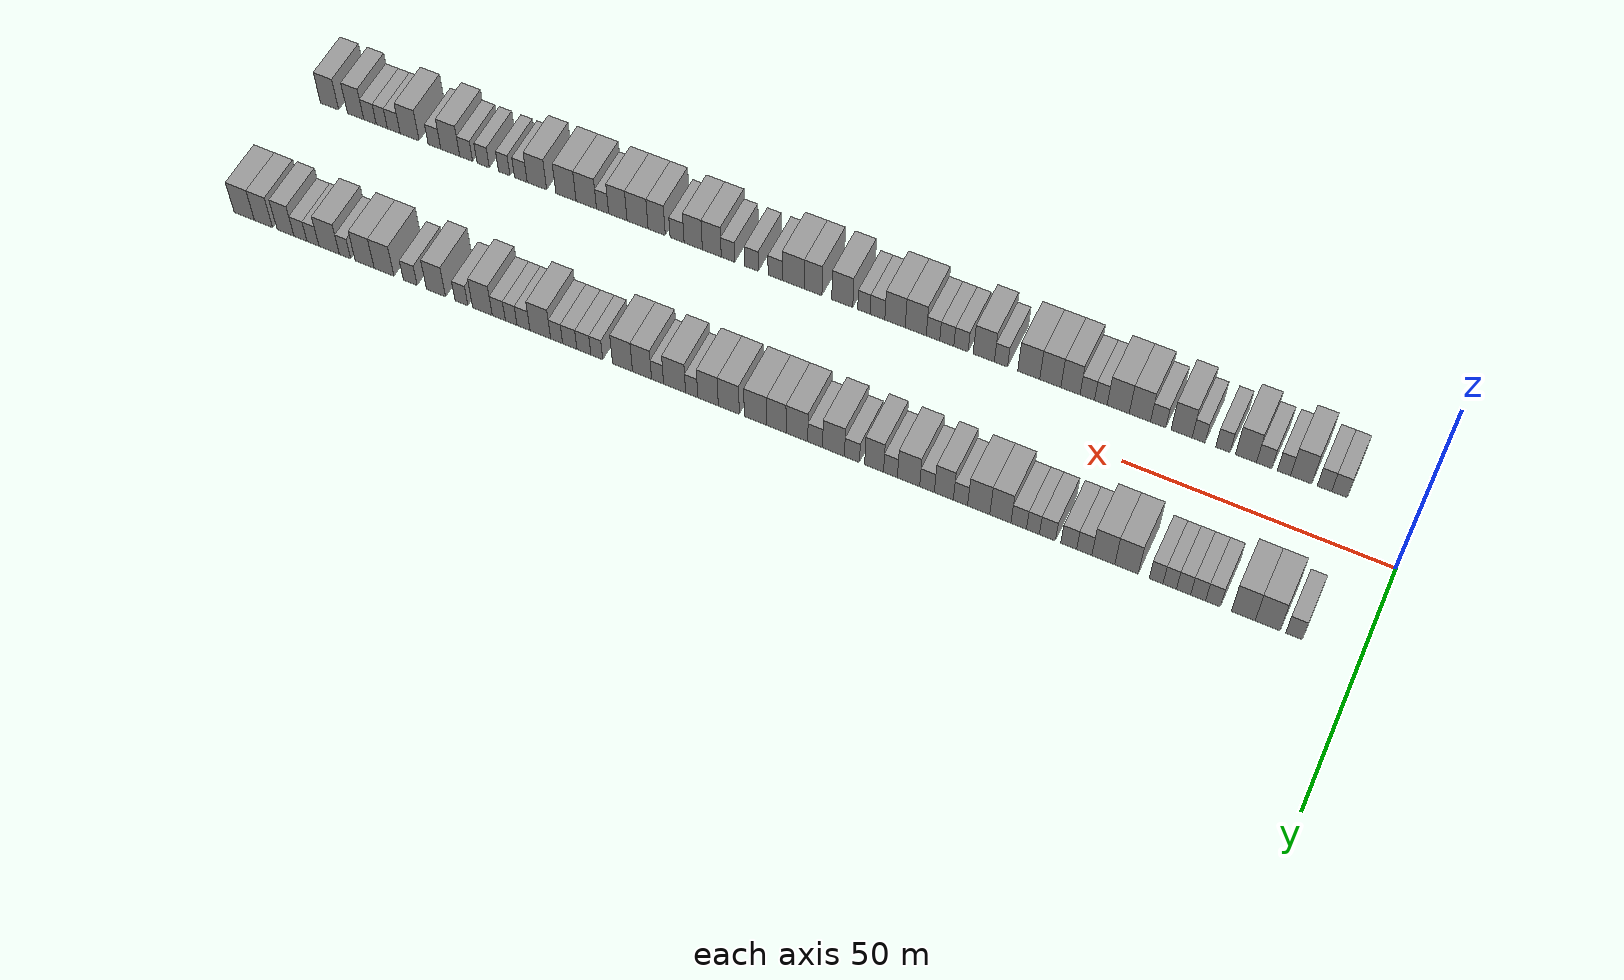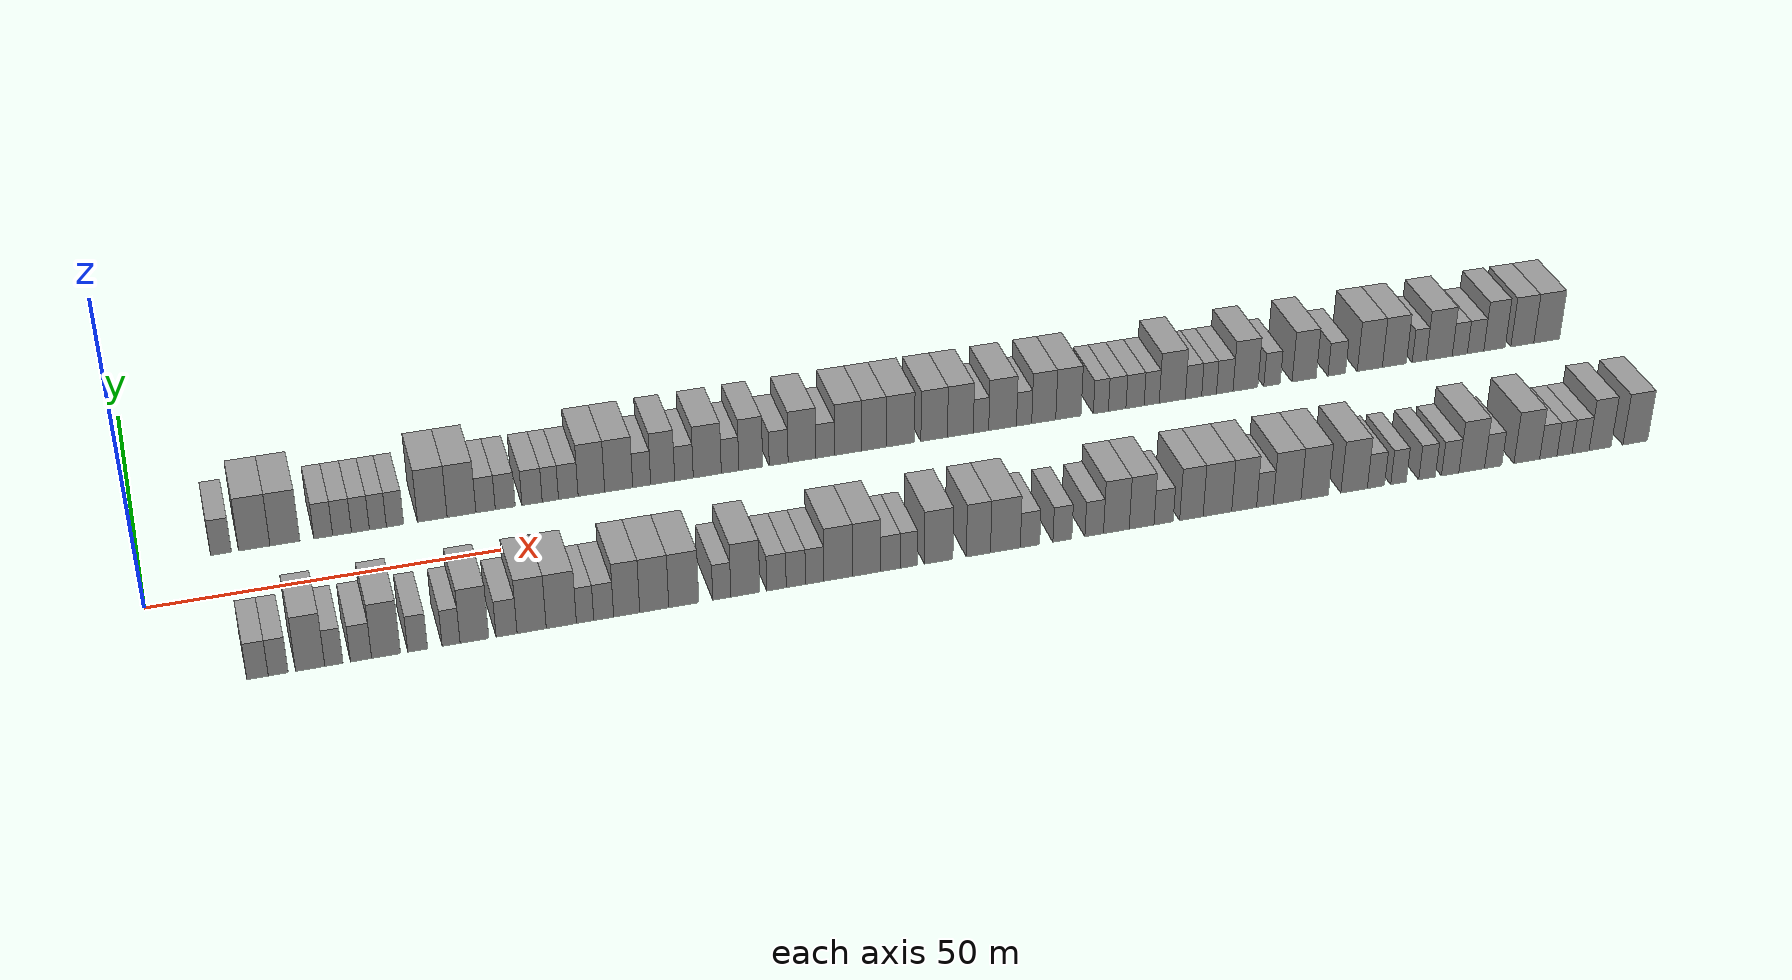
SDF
<sdf version="1.6">
 <world name="default">
  <scene>
   <sky><clouds><speed>12</speed></clouds></sky>
   <ambient>0.4 0.4 0.4 1</ambient>
   <background>0.7 0.7 0.7 1</background>
   <shadows>1</shadows>
  </scene>
  <gravity>0 0 -9.8066</gravity>
  <magnetic_field>6e-06 2.3e-05 -4.2e-05</magnetic_field>
  <physics default="0" name="default_physics" type="ode">
   <ode>
    <solver>
     <type>quick</type>
     <iters>10</iters>
     <sor>1.0</sor>
     <use_dynamic_moi_rescaling>0</use_dynamic_moi_rescaling>
    </solver>
    <constraints>
     <cfm>0</cfm>
     <erp>0.2</erp>
     <contact_max_correcting_vel>100</contact_max_correcting_vel>
     <contact_surface_layer>0.001</contact_surface_layer>
    </constraints>
   </ode>
   <max_step_size>0.004</max_step_size>
   <real_time_factor>1</real_time_factor>
   <real_time_update_rate>250</real_time_update_rate>
  </physics>
  <light name="sun" type="directional">
   <pose>0 0 10 0 0 0</pose>
   <diffuse>0.8 0.8 0.8 1</diffuse>
   <specular>0.2 0.2 0.2 1</specular>
   <attenuation>
    <range>1000</range>
    <constant>0.9</constant>
    <linear>0.01</linear>
    <quadratic>0.001</quadratic>
   </attenuation>
   <direction>-0.5 0.1 -0.9</direction>
  </light>
  <model name="building_1">
   <static>1</static>
   <pose>11.4720 15.0000 0 0.000000 0.000000 1.570796</pose>
   <link name="link">
    <pose>0 0 3.00 0 0 0</pose>
    <collision name="collision"><geometry><box><size>10.0000 2.9440 6.0000</size></box></geometry></collision>
    <visual name="visual">
     <cast_shadows>0</cast_shadows>
     <geometry><box><size>10.0000 2.9440 6.0000</size></box></geometry>
     <material>
      <script>
       <uri>model://grey_wall/materials/scripts</uri>
       <uri>model://grey_wall/materials/textures</uri>
       <name>vrc/grey_wall</name>
      </script>
     </material>
    </visual>
   </link>
  </model>
  <model name="building_2">
   <static>1</static>
   <pose>16.1658 15.0000 0 0.000000 0.000000 1.570796</pose>
   <link name="link">
    <pose>0 0 4.50 0 0 0</pose>
    <collision name="collision"><geometry><box><size>10.0000 4.4437 9.0000</size></box></geometry></collision>
    <visual name="visual">
     <cast_shadows>0</cast_shadows>
     <geometry><box><size>10.0000 4.4437 9.0000</size></box></geometry>
     <material>
      <script>
       <uri>model://grey_wall/materials/scripts</uri>
       <uri>model://grey_wall/materials/textures</uri>
       <name>vrc/grey_wall</name>
      </script>
     </material>
    </visual>
   </link>
  </model>
  <model name="building_3">
   <static>1</static>
   <pose>20.5180 15.0000 0 0.000000 0.000000 1.570796</pose>
   <link name="link">
    <pose>0 0 4.50 0 0 0</pose>
    <collision name="collision"><geometry><box><size>10.0000 4.2608 9.0000</size></box></geometry></collision>
    <visual name="visual">
     <cast_shadows>0</cast_shadows>
     <geometry><box><size>10.0000 4.2608 9.0000</size></box></geometry>
     <material>
      <script>
       <uri>model://grey_wall/materials/scripts</uri>
       <uri>model://grey_wall/materials/textures</uri>
       <name>vrc/grey_wall</name>
      </script>
     </material>
    </visual>
   </link>
  </model>
  <model name="building_4">
   <static>1</static>
   <pose>25.9887 15.0000 0 0.000000 0.000000 1.570796</pose>
   <link name="link">
    <pose>0 0 3.00 0 0 0</pose>
    <collision name="collision"><geometry><box><size>10.0000 2.6806 6.0000</size></box></geometry></collision>
    <visual name="visual">
     <cast_shadows>0</cast_shadows>
     <geometry><box><size>10.0000 2.6806 6.0000</size></box></geometry>
     <material>
      <script>
       <uri>model://grey_wall/materials/scripts</uri>
       <uri>model://grey_wall/materials/textures</uri>
       <name>vrc/grey_wall</name>
      </script>
     </material>
    </visual>
   </link>
  </model>
  <model name="building_5">
   <static>1</static>
   <pose>28.6825 15.0000 0 0.000000 0.000000 1.570796</pose>
   <link name="link">
    <pose>0 0 3.00 0 0 0</pose>
    <collision name="collision"><geometry><box><size>10.0000 2.7070 6.0000</size></box></geometry></collision>
    <visual name="visual">
     <cast_shadows>0</cast_shadows>
     <geometry><box><size>10.0000 2.7070 6.0000</size></box></geometry>
     <material>
      <script>
       <uri>model://grey_wall/materials/scripts</uri>
       <uri>model://grey_wall/materials/textures</uri>
       <name>vrc/grey_wall</name>
      </script>
     </material>
    </visual>
   </link>
  </model>
  <model name="building_6">
   <static>1</static>
   <pose>31.3200 15.0000 0 0.000000 0.000000 1.570796</pose>
   <link name="link">
    <pose>0 0 3.00 0 0 0</pose>
    <collision name="collision"><geometry><box><size>10.0000 2.5679 6.0000</size></box></geometry></collision>
    <visual name="visual">
     <cast_shadows>0</cast_shadows>
     <geometry><box><size>10.0000 2.5679 6.0000</size></box></geometry>
     <material>
      <script>
       <uri>model://grey_wall/materials/scripts</uri>
       <uri>model://grey_wall/materials/textures</uri>
       <name>vrc/grey_wall</name>
      </script>
     </material>
    </visual>
   </link>
  </model>
  <model name="building_7">
   <static>1</static>
   <pose>33.8323 15.0000 0 0.000000 0.000000 1.570796</pose>
   <link name="link">
    <pose>0 0 3.00 0 0 0</pose>
    <collision name="collision"><geometry><box><size>10.0000 2.4568 6.0000</size></box></geometry></collision>
    <visual name="visual">
     <cast_shadows>0</cast_shadows>
     <geometry><box><size>10.0000 2.4568 6.0000</size></box></geometry>
     <material>
      <script>
       <uri>model://grey_wall/materials/scripts</uri>
       <uri>model://grey_wall/materials/textures</uri>
       <name>vrc/grey_wall</name>
      </script>
     </material>
    </visual>
   </link>
  </model>
  <model name="building_8">
   <static>1</static>
   <pose>36.3138 15.0000 0 0.000000 0.000000 1.570796</pose>
   <link name="link">
    <pose>0 0 3.00 0 0 0</pose>
    <collision name="collision"><geometry><box><size>10.0000 2.5061 6.0000</size></box></geometry></collision>
    <visual name="visual">
     <cast_shadows>0</cast_shadows>
     <geometry><box><size>10.0000 2.5061 6.0000</size></box></geometry>
     <material>
      <script>
       <uri>model://grey_wall/materials/scripts</uri>
       <uri>model://grey_wall/materials/textures</uri>
       <name>vrc/grey_wall</name>
      </script>
     </material>
    </visual>
   </link>
  </model>
  <model name="building_9">
   <static>1</static>
   <pose>41.7231 15.0000 0 0.000000 0.000000 1.570796</pose>
   <link name="link">
    <pose>0 0 4.50 0 0 0</pose>
    <collision name="collision"><geometry><box><size>10.0000 4.3126 9.0000</size></box></geometry></collision>
    <visual name="visual">
     <cast_shadows>0</cast_shadows>
     <geometry><box><size>10.0000 4.3126 9.0000</size></box></geometry>
     <material>
      <script>
       <uri>model://grey_wall/materials/scripts</uri>
       <uri>model://grey_wall/materials/textures</uri>
       <name>vrc/grey_wall</name>
      </script>
     </material>
    </visual>
   </link>
  </model>
  <model name="building_10">
   <static>1</static>
   <pose>45.9907 15.0000 0 0.000000 0.000000 1.570796</pose>
   <link name="link">
    <pose>0 0 4.50 0 0 0</pose>
    <collision name="collision"><geometry><box><size>10.0000 4.2225 9.0000</size></box></geometry></collision>
    <visual name="visual">
     <cast_shadows>0</cast_shadows>
     <geometry><box><size>10.0000 4.2225 9.0000</size></box></geometry>
     <material>
      <script>
       <uri>model://grey_wall/materials/scripts</uri>
       <uri>model://grey_wall/materials/textures</uri>
       <name>vrc/grey_wall</name>
      </script>
     </material>
    </visual>
   </link>
  </model>
  <model name="building_11">
   <static>1</static>
   <pose>49.5140 15.0000 0 0.000000 0.000000 1.570796</pose>
   <link name="link">
    <pose>0 0 3.00 0 0 0</pose>
    <collision name="collision"><geometry><box><size>10.0000 2.8241 6.0000</size></box></geometry></collision>
    <visual name="visual">
     <cast_shadows>0</cast_shadows>
     <geometry><box><size>10.0000 2.8241 6.0000</size></box></geometry>
     <material>
      <script>
       <uri>model://grey_wall/materials/scripts</uri>
       <uri>model://grey_wall/materials/textures</uri>
       <name>vrc/grey_wall</name>
      </script>
     </material>
    </visual>
   </link>
  </model>
  <model name="building_12">
   <static>1</static>
   <pose>52.3961 15.0000 0 0.000000 0.000000 1.570796</pose>
   <link name="link">
    <pose>0 0 3.00 0 0 0</pose>
    <collision name="collision"><geometry><box><size>10.0000 2.9401 6.0000</size></box></geometry></collision>
    <visual name="visual">
     <cast_shadows>0</cast_shadows>
     <geometry><box><size>10.0000 2.9401 6.0000</size></box></geometry>
     <material>
      <script>
       <uri>model://grey_wall/materials/scripts</uri>
       <uri>model://grey_wall/materials/textures</uri>
       <name>vrc/grey_wall</name>
      </script>
     </material>
    </visual>
   </link>
  </model>
  <model name="building_13">
   <static>1</static>
   <pose>56.3581 15.0000 0 0.000000 0.000000 1.570796</pose>
   <link name="link">
    <pose>0 0 3.00 0 0 0</pose>
    <collision name="collision"><geometry><box><size>10.0000 2.9839 6.0000</size></box></geometry></collision>
    <visual name="visual">
     <cast_shadows>0</cast_shadows>
     <geometry><box><size>10.0000 2.9839 6.0000</size></box></geometry>
     <material>
      <script>
       <uri>model://grey_wall/materials/scripts</uri>
       <uri>model://grey_wall/materials/textures</uri>
       <name>vrc/grey_wall</name>
      </script>
     </material>
    </visual>
   </link>
  </model>
  <model name="building_14">
   <static>1</static>
   <pose>59.0586 15.0000 0 0.000000 0.000000 1.570796</pose>
   <link name="link">
    <pose>0 0 3.00 0 0 0</pose>
    <collision name="collision"><geometry><box><size>10.0000 2.4173 6.0000</size></box></geometry></collision>
    <visual name="visual">
     <cast_shadows>0</cast_shadows>
     <geometry><box><size>10.0000 2.4173 6.0000</size></box></geometry>
     <material>
      <script>
       <uri>model://grey_wall/materials/scripts</uri>
       <uri>model://grey_wall/materials/textures</uri>
       <name>vrc/grey_wall</name>
      </script>
     </material>
    </visual>
   </link>
  </model>
  <model name="building_15">
   <static>1</static>
   <pose>61.7267 15.0000 0 0.000000 0.000000 1.570796</pose>
   <link name="link">
    <pose>0 0 3.00 0 0 0</pose>
    <collision name="collision"><geometry><box><size>10.0000 2.9189 6.0000</size></box></geometry></collision>
    <visual name="visual">
     <cast_shadows>0</cast_shadows>
     <geometry><box><size>10.0000 2.9189 6.0000</size></box></geometry>
     <material>
      <script>
       <uri>model://grey_wall/materials/scripts</uri>
       <uri>model://grey_wall/materials/textures</uri>
       <name>vrc/grey_wall</name>
      </script>
     </material>
    </visual>
   </link>
  </model>
  <model name="building_16">
   <static>1</static>
   <pose>65.1740 15.0000 0 0.000000 0.000000 1.570796</pose>
   <link name="link">
    <pose>0 0 4.50 0 0 0</pose>
    <collision name="collision"><geometry><box><size>10.0000 3.9758 9.0000</size></box></geometry></collision>
    <visual name="visual">
     <cast_shadows>0</cast_shadows>
     <geometry><box><size>10.0000 3.9758 9.0000</size></box></geometry>
     <material>
      <script>
       <uri>model://grey_wall/materials/scripts</uri>
       <uri>model://grey_wall/materials/textures</uri>
       <name>vrc/grey_wall</name>
      </script>
     </material>
    </visual>
   </link>
  </model>
  <model name="building_17">
   <static>1</static>
   <pose>69.2637 15.0000 0 0.000000 0.000000 1.570796</pose>
   <link name="link">
    <pose>0 0 4.50 0 0 0</pose>
    <collision name="collision"><geometry><box><size>10.0000 4.2034 9.0000</size></box></geometry></collision>
    <visual name="visual">
     <cast_shadows>0</cast_shadows>
     <geometry><box><size>10.0000 4.2034 9.0000</size></box></geometry>
     <material>
      <script>
       <uri>model://grey_wall/materials/scripts</uri>
       <uri>model://grey_wall/materials/textures</uri>
       <name>vrc/grey_wall</name>
      </script>
     </material>
    </visual>
   </link>
  </model>
  <model name="building_18">
   <static>1</static>
   <pose>72.7155 15.0000 0 0.000000 0.000000 1.570796</pose>
   <link name="link">
    <pose>0 0 3.00 0 0 0</pose>
    <collision name="collision"><geometry><box><size>10.0000 2.7002 6.0000</size></box></geometry></collision>
    <visual name="visual">
     <cast_shadows>0</cast_shadows>
     <geometry><box><size>10.0000 2.7002 6.0000</size></box></geometry>
     <material>
      <script>
       <uri>model://grey_wall/materials/scripts</uri>
       <uri>model://grey_wall/materials/textures</uri>
       <name>vrc/grey_wall</name>
      </script>
     </material>
    </visual>
   </link>
  </model>
  <model name="building_19">
   <static>1</static>
   <pose>75.8764 15.0000 0 0.000000 0.000000 1.570796</pose>
   <link name="link">
    <pose>0 0 4.50 0 0 0</pose>
    <collision name="collision"><geometry><box><size>10.0000 3.6217 9.0000</size></box></geometry></collision>
    <visual name="visual">
     <cast_shadows>0</cast_shadows>
     <geometry><box><size>10.0000 3.6217 9.0000</size></box></geometry>
     <material>
      <script>
       <uri>model://grey_wall/materials/scripts</uri>
       <uri>model://grey_wall/materials/textures</uri>
       <name>vrc/grey_wall</name>
      </script>
     </material>
    </visual>
   </link>
  </model>
  <model name="building_20">
   <static>1</static>
   <pose>79.0913 15.0000 0 0.000000 0.000000 1.570796</pose>
   <link name="link">
    <pose>0 0 3.00 0 0 0</pose>
    <collision name="collision"><geometry><box><size>10.0000 2.8080 6.0000</size></box></geometry></collision>
    <visual name="visual">
     <cast_shadows>0</cast_shadows>
     <geometry><box><size>10.0000 2.8080 6.0000</size></box></geometry>
     <material>
      <script>
       <uri>model://grey_wall/materials/scripts</uri>
       <uri>model://grey_wall/materials/textures</uri>
       <name>vrc/grey_wall</name>
      </script>
     </material>
    </visual>
   </link>
  </model>
  <model name="building_21">
   <static>1</static>
   <pose>82.6306 15.0000 0 0.000000 0.000000 1.570796</pose>
   <link name="link">
    <pose>0 0 4.50 0 0 0</pose>
    <collision name="collision"><geometry><box><size>10.0000 4.2707 9.0000</size></box></geometry></collision>
    <visual name="visual">
     <cast_shadows>0</cast_shadows>
     <geometry><box><size>10.0000 4.2707 9.0000</size></box></geometry>
     <material>
      <script>
       <uri>model://grey_wall/materials/scripts</uri>
       <uri>model://grey_wall/materials/textures</uri>
       <name>vrc/grey_wall</name>
      </script>
     </material>
    </visual>
   </link>
  </model>
  <model name="building_22">
   <static>1</static>
   <pose>86.1015 15.0000 0 0.000000 0.000000 1.570796</pose>
   <link name="link">
    <pose>0 0 3.00 0 0 0</pose>
    <collision name="collision"><geometry><box><size>10.0000 2.6711 6.0000</size></box></geometry></collision>
    <visual name="visual">
     <cast_shadows>0</cast_shadows>
     <geometry><box><size>10.0000 2.6711 6.0000</size></box></geometry>
     <material>
      <script>
       <uri>model://grey_wall/materials/scripts</uri>
       <uri>model://grey_wall/materials/textures</uri>
       <name>vrc/grey_wall</name>
      </script>
     </material>
    </visual>
   </link>
  </model>
  <model name="building_23">
   <static>1</static>
   <pose>89.2615 15.0000 0 0.000000 0.000000 1.570796</pose>
   <link name="link">
    <pose>0 0 4.50 0 0 0</pose>
    <collision name="collision"><geometry><box><size>10.0000 3.6487 9.0000</size></box></geometry></collision>
    <visual name="visual">
     <cast_shadows>0</cast_shadows>
     <geometry><box><size>10.0000 3.6487 9.0000</size></box></geometry>
     <material>
      <script>
       <uri>model://grey_wall/materials/scripts</uri>
       <uri>model://grey_wall/materials/textures</uri>
       <name>vrc/grey_wall</name>
      </script>
     </material>
    </visual>
   </link>
  </model>
  <model name="building_24">
   <static>1</static>
   <pose>93.5392 15.0000 0 0.000000 0.000000 1.570796</pose>
   <link name="link">
    <pose>0 0 3.00 0 0 0</pose>
    <collision name="collision"><geometry><box><size>10.0000 2.9068 6.0000</size></box></geometry></collision>
    <visual name="visual">
     <cast_shadows>0</cast_shadows>
     <geometry><box><size>10.0000 2.9068 6.0000</size></box></geometry>
     <material>
      <script>
       <uri>model://grey_wall/materials/scripts</uri>
       <uri>model://grey_wall/materials/textures</uri>
       <name>vrc/grey_wall</name>
      </script>
     </material>
    </visual>
   </link>
  </model>
  <model name="building_25">
   <static>1</static>
   <pose>97.1239 15.0000 0 0.000000 0.000000 1.570796</pose>
   <link name="link">
    <pose>0 0 4.50 0 0 0</pose>
    <collision name="collision"><geometry><box><size>10.0000 4.2625 9.0000</size></box></geometry></collision>
    <visual name="visual">
     <cast_shadows>0</cast_shadows>
     <geometry><box><size>10.0000 4.2625 9.0000</size></box></geometry>
     <material>
      <script>
       <uri>model://grey_wall/materials/scripts</uri>
       <uri>model://grey_wall/materials/textures</uri>
       <name>vrc/grey_wall</name>
      </script>
     </material>
    </visual>
   </link>
  </model>
  <model name="building_26">
   <static>1</static>
   <pose>100.7043 15.0000 0 0.000000 0.000000 1.570796</pose>
   <link name="link">
    <pose>0 0 3.00 0 0 0</pose>
    <collision name="collision"><geometry><box><size>10.0000 2.8983 6.0000</size></box></geometry></collision>
    <visual name="visual">
     <cast_shadows>0</cast_shadows>
     <geometry><box><size>10.0000 2.8983 6.0000</size></box></geometry>
     <material>
      <script>
       <uri>model://grey_wall/materials/scripts</uri>
       <uri>model://grey_wall/materials/textures</uri>
       <name>vrc/grey_wall</name>
      </script>
     </material>
    </visual>
   </link>
  </model>
  <model name="building_27">
   <static>1</static>
   <pose>104.2949 15.0000 0 0.000000 0.000000 1.570796</pose>
   <link name="link">
    <pose>0 0 4.50 0 0 0</pose>
    <collision name="collision"><geometry><box><size>10.0000 4.2830 9.0000</size></box></geometry></collision>
    <visual name="visual">
     <cast_shadows>0</cast_shadows>
     <geometry><box><size>10.0000 4.2830 9.0000</size></box></geometry>
     <material>
      <script>
       <uri>model://grey_wall/materials/scripts</uri>
       <uri>model://grey_wall/materials/textures</uri>
       <name>vrc/grey_wall</name>
      </script>
     </material>
    </visual>
   </link>
  </model>
  <model name="building_28">
   <static>1</static>
   <pose>108.3185 15.0000 0 0.000000 0.000000 1.570796</pose>
   <link name="link">
    <pose>0 0 4.50 0 0 0</pose>
    <collision name="collision"><geometry><box><size>10.0000 3.7640 9.0000</size></box></geometry></collision>
    <visual name="visual">
     <cast_shadows>0</cast_shadows>
     <geometry><box><size>10.0000 3.7640 9.0000</size></box></geometry>
     <material>
      <script>
       <uri>model://grey_wall/materials/scripts</uri>
       <uri>model://grey_wall/materials/textures</uri>
       <name>vrc/grey_wall</name>
      </script>
     </material>
    </visual>
   </link>
  </model>
  <model name="building_29">
   <static>1</static>
   <pose>112.4363 15.0000 0 0.000000 0.000000 1.570796</pose>
   <link name="link">
    <pose>0 0 4.50 0 0 0</pose>
    <collision name="collision"><geometry><box><size>10.0000 4.4717 9.0000</size></box></geometry></collision>
    <visual name="visual">
     <cast_shadows>0</cast_shadows>
     <geometry><box><size>10.0000 4.4717 9.0000</size></box></geometry>
     <material>
      <script>
       <uri>model://grey_wall/materials/scripts</uri>
       <uri>model://grey_wall/materials/textures</uri>
       <name>vrc/grey_wall</name>
      </script>
     </material>
    </visual>
   </link>
  </model>
  <model name="building_30">
   <static>1</static>
   <pose>117.7677 15.0000 0 0.000000 0.000000 1.570796</pose>
   <link name="link">
    <pose>0 0 4.50 0 0 0</pose>
    <collision name="collision"><geometry><box><size>10.0000 4.1911 9.0000</size></box></geometry></collision>
    <visual name="visual">
     <cast_shadows>0</cast_shadows>
     <geometry><box><size>10.0000 4.1911 9.0000</size></box></geometry>
     <material>
      <script>
       <uri>model://grey_wall/materials/scripts</uri>
       <uri>model://grey_wall/materials/textures</uri>
       <name>vrc/grey_wall</name>
      </script>
     </material>
    </visual>
   </link>
  </model>
  <model name="building_31">
   <static>1</static>
   <pose>121.9125 15.0000 0 0.000000 0.000000 1.570796</pose>
   <link name="link">
    <pose>0 0 4.50 0 0 0</pose>
    <collision name="collision"><geometry><box><size>10.0000 4.0984 9.0000</size></box></geometry></collision>
    <visual name="visual">
     <cast_shadows>0</cast_shadows>
     <geometry><box><size>10.0000 4.0984 9.0000</size></box></geometry>
     <material>
      <script>
       <uri>model://grey_wall/materials/scripts</uri>
       <uri>model://grey_wall/materials/textures</uri>
       <name>vrc/grey_wall</name>
      </script>
     </material>
    </visual>
   </link>
  </model>
  <model name="building_32">
   <static>1</static>
   <pose>125.1835 15.0000 0 0.000000 0.000000 1.570796</pose>
   <link name="link">
    <pose>0 0 3.00 0 0 0</pose>
    <collision name="collision"><geometry><box><size>10.0000 2.4436 6.0000</size></box></geometry></collision>
    <visual name="visual">
     <cast_shadows>0</cast_shadows>
     <geometry><box><size>10.0000 2.4436 6.0000</size></box></geometry>
     <material>
      <script>
       <uri>model://grey_wall/materials/scripts</uri>
       <uri>model://grey_wall/materials/textures</uri>
       <name>vrc/grey_wall</name>
      </script>
     </material>
    </visual>
   </link>
  </model>
  <model name="building_33">
   <static>1</static>
   <pose>128.6230 15.0000 0 0.000000 0.000000 1.570796</pose>
   <link name="link">
    <pose>0 0 4.50 0 0 0</pose>
    <collision name="collision"><geometry><box><size>10.0000 4.4353 9.0000</size></box></geometry></collision>
    <visual name="visual">
     <cast_shadows>0</cast_shadows>
     <geometry><box><size>10.0000 4.4353 9.0000</size></box></geometry>
     <material>
      <script>
       <uri>model://grey_wall/materials/scripts</uri>
       <uri>model://grey_wall/materials/textures</uri>
       <name>vrc/grey_wall</name>
      </script>
     </material>
    </visual>
   </link>
  </model>
  <model name="building_34">
   <static>1</static>
   <pose>132.0591 15.0000 0 0.000000 0.000000 1.570796</pose>
   <link name="link">
    <pose>0 0 3.00 0 0 0</pose>
    <collision name="collision"><geometry><box><size>10.0000 2.4370 6.0000</size></box></geometry></collision>
    <visual name="visual">
     <cast_shadows>0</cast_shadows>
     <geometry><box><size>10.0000 2.4370 6.0000</size></box></geometry>
     <material>
      <script>
       <uri>model://grey_wall/materials/scripts</uri>
       <uri>model://grey_wall/materials/textures</uri>
       <name>vrc/grey_wall</name>
      </script>
     </material>
    </visual>
   </link>
  </model>
  <model name="building_35">
   <static>1</static>
   <pose>135.2093 15.0000 0 0.000000 0.000000 1.570796</pose>
   <link name="link">
    <pose>0 0 4.50 0 0 0</pose>
    <collision name="collision"><geometry><box><size>10.0000 3.8633 9.0000</size></box></geometry></collision>
    <visual name="visual">
     <cast_shadows>0</cast_shadows>
     <geometry><box><size>10.0000 3.8633 9.0000</size></box></geometry>
     <material>
      <script>
       <uri>model://grey_wall/materials/scripts</uri>
       <uri>model://grey_wall/materials/textures</uri>
       <name>vrc/grey_wall</name>
      </script>
     </material>
    </visual>
   </link>
  </model>
  <model name="building_36">
   <static>1</static>
   <pose>139.1776 15.0000 0 0.000000 0.000000 1.570796</pose>
   <link name="link">
    <pose>0 0 4.50 0 0 0</pose>
    <collision name="collision"><geometry><box><size>10.0000 4.0733 9.0000</size></box></geometry></collision>
    <visual name="visual">
     <cast_shadows>0</cast_shadows>
     <geometry><box><size>10.0000 4.0733 9.0000</size></box></geometry>
     <material>
      <script>
       <uri>model://grey_wall/materials/scripts</uri>
       <uri>model://grey_wall/materials/textures</uri>
       <name>vrc/grey_wall</name>
      </script>
     </material>
    </visual>
   </link>
  </model>
  <model name="building_37">
   <static>1</static>
   <pose>144.4337 15.0000 0 0.000000 0.000000 1.570796</pose>
   <link name="link">
    <pose>0 0 3.00 0 0 0</pose>
    <collision name="collision"><geometry><box><size>10.0000 2.4388 6.0000</size></box></geometry></collision>
    <visual name="visual">
     <cast_shadows>0</cast_shadows>
     <geometry><box><size>10.0000 2.4388 6.0000</size></box></geometry>
     <material>
      <script>
       <uri>model://grey_wall/materials/scripts</uri>
       <uri>model://grey_wall/materials/textures</uri>
       <name>vrc/grey_wall</name>
      </script>
     </material>
    </visual>
   </link>
  </model>
  <model name="building_38">
   <static>1</static>
   <pose>147.0817 15.0000 0 0.000000 0.000000 1.570796</pose>
   <link name="link">
    <pose>0 0 3.00 0 0 0</pose>
    <collision name="collision"><geometry><box><size>10.0000 2.8573 6.0000</size></box></geometry></collision>
    <visual name="visual">
     <cast_shadows>0</cast_shadows>
     <geometry><box><size>10.0000 2.8573 6.0000</size></box></geometry>
     <material>
      <script>
       <uri>model://grey_wall/materials/scripts</uri>
       <uri>model://grey_wall/materials/textures</uri>
       <name>vrc/grey_wall</name>
      </script>
     </material>
    </visual>
   </link>
  </model>
  <model name="building_39">
   <static>1</static>
   <pose>149.9892 15.0000 0 0.000000 0.000000 1.570796</pose>
   <link name="link">
    <pose>0 0 3.00 0 0 0</pose>
    <collision name="collision"><geometry><box><size>10.0000 2.9577 6.0000</size></box></geometry></collision>
    <visual name="visual">
     <cast_shadows>0</cast_shadows>
     <geometry><box><size>10.0000 2.9577 6.0000</size></box></geometry>
     <material>
      <script>
       <uri>model://grey_wall/materials/scripts</uri>
       <uri>model://grey_wall/materials/textures</uri>
       <name>vrc/grey_wall</name>
      </script>
     </material>
    </visual>
   </link>
  </model>
  <model name="building_40">
   <static>1</static>
   <pose>152.7050 15.0000 0 0.000000 0.000000 1.570796</pose>
   <link name="link">
    <pose>0 0 3.00 0 0 0</pose>
    <collision name="collision"><geometry><box><size>10.0000 2.4739 6.0000</size></box></geometry></collision>
    <visual name="visual">
     <cast_shadows>0</cast_shadows>
     <geometry><box><size>10.0000 2.4739 6.0000</size></box></geometry>
     <material>
      <script>
       <uri>model://grey_wall/materials/scripts</uri>
       <uri>model://grey_wall/materials/textures</uri>
       <name>vrc/grey_wall</name>
      </script>
     </material>
    </visual>
   </link>
  </model>
  <model name="building_41">
   <static>1</static>
   <pose>156.0827 15.0000 0 0.000000 0.000000 1.570796</pose>
   <link name="link">
    <pose>0 0 4.50 0 0 0</pose>
    <collision name="collision"><geometry><box><size>10.0000 4.2815 9.0000</size></box></geometry></collision>
    <visual name="visual">
     <cast_shadows>0</cast_shadows>
     <geometry><box><size>10.0000 4.2815 9.0000</size></box></geometry>
     <material>
      <script>
       <uri>model://grey_wall/materials/scripts</uri>
       <uri>model://grey_wall/materials/textures</uri>
       <name>vrc/grey_wall</name>
      </script>
     </material>
    </visual>
   </link>
  </model>
  <model name="building_42">
   <static>1</static>
   <pose>159.5707 15.0000 0 0.000000 0.000000 1.570796</pose>
   <link name="link">
    <pose>0 0 3.00 0 0 0</pose>
    <collision name="collision"><geometry><box><size>10.0000 2.6945 6.0000</size></box></geometry></collision>
    <visual name="visual">
     <cast_shadows>0</cast_shadows>
     <geometry><box><size>10.0000 2.6945 6.0000</size></box></geometry>
     <material>
      <script>
       <uri>model://grey_wall/materials/scripts</uri>
       <uri>model://grey_wall/materials/textures</uri>
       <name>vrc/grey_wall</name>
      </script>
     </material>
    </visual>
   </link>
  </model>
  <model name="building_43">
   <static>1</static>
   <pose>162.1420 15.0000 0 0.000000 0.000000 1.570796</pose>
   <link name="link">
    <pose>0 0 3.00 0 0 0</pose>
    <collision name="collision"><geometry><box><size>10.0000 2.4482 6.0000</size></box></geometry></collision>
    <visual name="visual">
     <cast_shadows>0</cast_shadows>
     <geometry><box><size>10.0000 2.4482 6.0000</size></box></geometry>
     <material>
      <script>
       <uri>model://grey_wall/materials/scripts</uri>
       <uri>model://grey_wall/materials/textures</uri>
       <name>vrc/grey_wall</name>
      </script>
     </material>
    </visual>
   </link>
  </model>
  <model name="building_44">
   <static>1</static>
   <pose>164.7349 15.0000 0 0.000000 0.000000 1.570796</pose>
   <link name="link">
    <pose>0 0 3.00 0 0 0</pose>
    <collision name="collision"><geometry><box><size>10.0000 2.7376 6.0000</size></box></geometry></collision>
    <visual name="visual">
     <cast_shadows>0</cast_shadows>
     <geometry><box><size>10.0000 2.7376 6.0000</size></box></geometry>
     <material>
      <script>
       <uri>model://grey_wall/materials/scripts</uri>
       <uri>model://grey_wall/materials/textures</uri>
       <name>vrc/grey_wall</name>
      </script>
     </material>
    </visual>
   </link>
  </model>
  <model name="building_45">
   <static>1</static>
   <pose>168.1659 15.0000 0 0.000000 0.000000 1.570796</pose>
   <link name="link">
    <pose>0 0 4.50 0 0 0</pose>
    <collision name="collision"><geometry><box><size>10.0000 4.1245 9.0000</size></box></geometry></collision>
    <visual name="visual">
     <cast_shadows>0</cast_shadows>
     <geometry><box><size>10.0000 4.1245 9.0000</size></box></geometry>
     <material>
      <script>
       <uri>model://grey_wall/materials/scripts</uri>
       <uri>model://grey_wall/materials/textures</uri>
       <name>vrc/grey_wall</name>
      </script>
     </material>
    </visual>
   </link>
  </model>
  <model name="building_46">
   <static>1</static>
   <pose>172.5894 15.0000 0 0.000000 0.000000 1.570796</pose>
   <link name="link">
    <pose>0 0 3.00 0 0 0</pose>
    <collision name="collision"><geometry><box><size>10.0000 2.7224 6.0000</size></box></geometry></collision>
    <visual name="visual">
     <cast_shadows>0</cast_shadows>
     <geometry><box><size>10.0000 2.7224 6.0000</size></box></geometry>
     <material>
      <script>
       <uri>model://grey_wall/materials/scripts</uri>
       <uri>model://grey_wall/materials/textures</uri>
       <name>vrc/grey_wall</name>
      </script>
     </material>
    </visual>
   </link>
  </model>
  <model name="building_47">
   <static>1</static>
   <pose>177.9685 15.0000 0 0.000000 0.000000 1.570796</pose>
   <link name="link">
    <pose>0 0 4.50 0 0 0</pose>
    <collision name="collision"><geometry><box><size>10.0000 4.0358 9.0000</size></box></geometry></collision>
    <visual name="visual">
     <cast_shadows>0</cast_shadows>
     <geometry><box><size>10.0000 4.0358 9.0000</size></box></geometry>
     <material>
      <script>
       <uri>model://grey_wall/materials/scripts</uri>
       <uri>model://grey_wall/materials/textures</uri>
       <name>vrc/grey_wall</name>
      </script>
     </material>
    </visual>
   </link>
  </model>
  <model name="building_48">
   <static>1</static>
   <pose>183.4565 15.0000 0 0.000000 0.000000 1.570796</pose>
   <link name="link">
    <pose>0 0 3.00 0 0 0</pose>
    <collision name="collision"><geometry><box><size>10.0000 2.9402 6.0000</size></box></geometry></collision>
    <visual name="visual">
     <cast_shadows>0</cast_shadows>
     <geometry><box><size>10.0000 2.9402 6.0000</size></box></geometry>
     <material>
      <script>
       <uri>model://grey_wall/materials/scripts</uri>
       <uri>model://grey_wall/materials/textures</uri>
       <name>vrc/grey_wall</name>
      </script>
     </material>
    </visual>
   </link>
  </model>
  <model name="building_49">
   <static>1</static>
   <pose>189.0600 15.0000 0 0.000000 0.000000 1.570796</pose>
   <link name="link">
    <pose>0 0 4.50 0 0 0</pose>
    <collision name="collision"><geometry><box><size>10.0000 4.2668 9.0000</size></box></geometry></collision>
    <visual name="visual">
     <cast_shadows>0</cast_shadows>
     <geometry><box><size>10.0000 4.2668 9.0000</size></box></geometry>
     <material>
      <script>
       <uri>model://grey_wall/materials/scripts</uri>
       <uri>model://grey_wall/materials/textures</uri>
       <name>vrc/grey_wall</name>
      </script>
     </material>
    </visual>
   </link>
  </model>
  <model name="building_50">
   <static>1</static>
   <pose>193.2329 15.0000 0 0.000000 0.000000 1.570796</pose>
   <link name="link">
    <pose>0 0 4.50 0 0 0</pose>
    <collision name="collision"><geometry><box><size>10.0000 4.0790 9.0000</size></box></geometry></collision>
    <visual name="visual">
     <cast_shadows>0</cast_shadows>
     <geometry><box><size>10.0000 4.0790 9.0000</size></box></geometry>
     <material>
      <script>
       <uri>model://grey_wall/materials/scripts</uri>
       <uri>model://grey_wall/materials/textures</uri>
       <name>vrc/grey_wall</name>
      </script>
     </material>
    </visual>
   </link>
  </model>
  <model name="building_51">
   <static>1</static>
   <pose>197.4810 15.0000 0 0.000000 0.000000 1.570796</pose>
   <link name="link">
    <pose>0 0 3.00 0 0 0</pose>
    <collision name="collision"><geometry><box><size>10.0000 2.4172 6.0000</size></box></geometry></collision>
    <visual name="visual">
     <cast_shadows>0</cast_shadows>
     <geometry><box><size>10.0000 2.4172 6.0000</size></box></geometry>
     <material>
      <script>
       <uri>model://grey_wall/materials/scripts</uri>
       <uri>model://grey_wall/materials/textures</uri>
       <name>vrc/grey_wall</name>
      </script>
     </material>
    </visual>
   </link>
  </model>
  <model name="building_52">
   <static>1</static>
   <pose>200.9141 15.0000 0 0.000000 0.000000 1.570796</pose>
   <link name="link">
    <pose>0 0 4.50 0 0 0</pose>
    <collision name="collision"><geometry><box><size>10.0000 4.4492 9.0000</size></box></geometry></collision>
    <visual name="visual">
     <cast_shadows>0</cast_shadows>
     <geometry><box><size>10.0000 4.4492 9.0000</size></box></geometry>
     <material>
      <script>
       <uri>model://grey_wall/materials/scripts</uri>
       <uri>model://grey_wall/materials/textures</uri>
       <name>vrc/grey_wall</name>
      </script>
     </material>
    </visual>
   </link>
  </model>
  <model name="building_53">
   <static>1</static>
   <pose>204.4451 15.0000 0 0.000000 0.000000 1.570796</pose>
   <link name="link">
    <pose>0 0 3.00 0 0 0</pose>
    <collision name="collision"><geometry><box><size>10.0000 2.6127 6.0000</size></box></geometry></collision>
    <visual name="visual">
     <cast_shadows>0</cast_shadows>
     <geometry><box><size>10.0000 2.6127 6.0000</size></box></geometry>
     <material>
      <script>
       <uri>model://grey_wall/materials/scripts</uri>
       <uri>model://grey_wall/materials/textures</uri>
       <name>vrc/grey_wall</name>
      </script>
     </material>
    </visual>
   </link>
  </model>
  <model name="building_54">
   <static>1</static>
   <pose>207.1741 15.0000 0 0.000000 0.000000 1.570796</pose>
   <link name="link">
    <pose>0 0 3.00 0 0 0</pose>
    <collision name="collision"><geometry><box><size>10.0000 2.8453 6.0000</size></box></geometry></collision>
    <visual name="visual">
     <cast_shadows>0</cast_shadows>
     <geometry><box><size>10.0000 2.8453 6.0000</size></box></geometry>
     <material>
      <script>
       <uri>model://grey_wall/materials/scripts</uri>
       <uri>model://grey_wall/materials/textures</uri>
       <name>vrc/grey_wall</name>
      </script>
     </material>
    </visual>
   </link>
  </model>
  <model name="building_55">
   <static>1</static>
   <pose>210.4482 15.0000 0 0.000000 0.000000 1.570796</pose>
   <link name="link">
    <pose>0 0 4.50 0 0 0</pose>
    <collision name="collision"><geometry><box><size>10.0000 3.7030 9.0000</size></box></geometry></collision>
    <visual name="visual">
     <cast_shadows>0</cast_shadows>
     <geometry><box><size>10.0000 3.7030 9.0000</size></box></geometry>
     <material>
      <script>
       <uri>model://grey_wall/materials/scripts</uri>
       <uri>model://grey_wall/materials/textures</uri>
       <name>vrc/grey_wall</name>
      </script>
     </material>
    </visual>
   </link>
  </model>
  <model name="building_56">
   <static>1</static>
   <pose>215.3000 15.0000 0 0.000000 0.000000 1.570796</pose>
   <link name="link">
    <pose>0 0 4.50 0 0 0</pose>
    <collision name="collision"><geometry><box><size>10.0000 4.0005 9.0000</size></box></geometry></collision>
    <visual name="visual">
     <cast_shadows>0</cast_shadows>
     <geometry><box><size>10.0000 4.0005 9.0000</size></box></geometry>
     <material>
      <script>
       <uri>model://grey_wall/materials/scripts</uri>
       <uri>model://grey_wall/materials/textures</uri>
       <name>vrc/grey_wall</name>
      </script>
     </material>
    </visual>
   </link>
  </model>
  <model name="building_57">
   <static>1</static>
   <pose>219.5422 15.0000 0 0.000000 0.000000 1.570796</pose>
   <link name="link">
    <pose>0 0 4.50 0 0 0</pose>
    <collision name="collision"><geometry><box><size>10.0000 4.4840 9.0000</size></box></geometry></collision>
    <visual name="visual">
     <cast_shadows>0</cast_shadows>
     <geometry><box><size>10.0000 4.4840 9.0000</size></box></geometry>
     <material>
      <script>
       <uri>model://grey_wall/materials/scripts</uri>
       <uri>model://grey_wall/materials/textures</uri>
       <name>vrc/grey_wall</name>
      </script>
     </material>
    </visual>
   </link>
  </model>
  <model name="building_58">
   <static>1</static>
   <pose>13.4286 -15.0000 0 0.000000 0.000000 1.570796</pose>
   <link name="link">
    <pose>0 0 3.00 0 0 0</pose>
    <collision name="collision"><geometry><box><size>10.0000 2.8573 6.0000</size></box></geometry></collision>
    <visual name="visual">
     <cast_shadows>0</cast_shadows>
     <geometry><box><size>10.0000 2.8573 6.0000</size></box></geometry>
     <material>
      <script>
       <uri>model://grey_wall/materials/scripts</uri>
       <uri>model://grey_wall/materials/textures</uri>
       <name>vrc/grey_wall</name>
      </script>
     </material>
    </visual>
   </link>
  </model>
  <model name="building_59">
   <static>1</static>
   <pose>16.1869 -15.0000 0 0.000000 0.000000 1.570796</pose>
   <link name="link">
    <pose>0 0 3.00 0 0 0</pose>
    <collision name="collision"><geometry><box><size>10.0000 2.6592 6.0000</size></box></geometry></collision>
    <visual name="visual">
     <cast_shadows>0</cast_shadows>
     <geometry><box><size>10.0000 2.6592 6.0000</size></box></geometry>
     <material>
      <script>
       <uri>model://grey_wall/materials/scripts</uri>
       <uri>model://grey_wall/materials/textures</uri>
       <name>vrc/grey_wall</name>
      </script>
     </material>
    </visual>
   </link>
  </model>
  <model name="building_60">
   <static>1</static>
   <pose>20.4738 -15.0000 0 0.000000 0.000000 1.570796</pose>
   <link name="link">
    <pose>0 0 4.50 0 0 0</pose>
    <collision name="collision"><geometry><box><size>10.0000 3.9146 9.0000</size></box></geometry></collision>
    <visual name="visual">
     <cast_shadows>0</cast_shadows>
     <geometry><box><size>10.0000 3.9146 9.0000</size></box></geometry>
     <material>
      <script>
       <uri>model://grey_wall/materials/scripts</uri>
       <uri>model://grey_wall/materials/textures</uri>
       <name>vrc/grey_wall</name>
      </script>
     </material>
    </visual>
   </link>
  </model>
  <model name="building_61">
   <static>1</static>
   <pose>23.6617 -15.0000 0 0.000000 0.000000 1.570796</pose>
   <link name="link">
    <pose>0 0 3.00 0 0 0</pose>
    <collision name="collision"><geometry><box><size>10.0000 2.4613 6.0000</size></box></geometry></collision>
    <visual name="visual">
     <cast_shadows>0</cast_shadows>
     <geometry><box><size>10.0000 2.4613 6.0000</size></box></geometry>
     <material>
      <script>
       <uri>model://grey_wall/materials/scripts</uri>
       <uri>model://grey_wall/materials/textures</uri>
       <name>vrc/grey_wall</name>
      </script>
     </material>
    </visual>
   </link>
  </model>
  <model name="building_62">
   <static>1</static>
   <pose>27.3281 -15.0000 0 0.000000 0.000000 1.570796</pose>
   <link name="link">
    <pose>0 0 3.00 0 0 0</pose>
    <collision name="collision"><geometry><box><size>10.0000 2.8715 6.0000</size></box></geometry></collision>
    <visual name="visual">
     <cast_shadows>0</cast_shadows>
     <geometry><box><size>10.0000 2.8715 6.0000</size></box></geometry>
     <material>
      <script>
       <uri>model://grey_wall/materials/scripts</uri>
       <uri>model://grey_wall/materials/textures</uri>
       <name>vrc/grey_wall</name>
      </script>
     </material>
    </visual>
   </link>
  </model>
  <model name="building_63">
   <static>1</static>
   <pose>30.7257 -15.0000 0 0.000000 0.000000 1.570796</pose>
   <link name="link">
    <pose>0 0 4.50 0 0 0</pose>
    <collision name="collision"><geometry><box><size>10.0000 3.9237 9.0000</size></box></geometry></collision>
    <visual name="visual">
     <cast_shadows>0</cast_shadows>
     <geometry><box><size>10.0000 3.9237 9.0000</size></box></geometry>
     <material>
      <script>
       <uri>model://grey_wall/materials/scripts</uri>
       <uri>model://grey_wall/materials/textures</uri>
       <name>vrc/grey_wall</name>
      </script>
     </material>
    </visual>
   </link>
  </model>
  <model name="building_64">
   <static>1</static>
   <pose>35.0339 -15.0000 0 0.000000 0.000000 1.570796</pose>
   <link name="link">
    <pose>0 0 3.00 0 0 0</pose>
    <collision name="collision"><geometry><box><size>10.0000 2.6927 6.0000</size></box></geometry></collision>
    <visual name="visual">
     <cast_shadows>0</cast_shadows>
     <geometry><box><size>10.0000 2.6927 6.0000</size></box></geometry>
     <material>
      <script>
       <uri>model://grey_wall/materials/scripts</uri>
       <uri>model://grey_wall/materials/textures</uri>
       <name>vrc/grey_wall</name>
      </script>
     </material>
    </visual>
   </link>
  </model>
  <model name="building_65">
   <static>1</static>
   <pose>39.6111 -15.0000 0 0.000000 0.000000 1.570796</pose>
   <link name="link">
    <pose>0 0 3.00 0 0 0</pose>
    <collision name="collision"><geometry><box><size>10.0000 2.4617 6.0000</size></box></geometry></collision>
    <visual name="visual">
     <cast_shadows>0</cast_shadows>
     <geometry><box><size>10.0000 2.4617 6.0000</size></box></geometry>
     <material>
      <script>
       <uri>model://grey_wall/materials/scripts</uri>
       <uri>model://grey_wall/materials/textures</uri>
       <name>vrc/grey_wall</name>
      </script>
     </material>
    </visual>
   </link>
  </model>
  <model name="building_66">
   <static>1</static>
   <pose>42.8222 -15.0000 0 0.000000 0.000000 1.570796</pose>
   <link name="link">
    <pose>0 0 4.50 0 0 0</pose>
    <collision name="collision"><geometry><box><size>10.0000 3.9605 9.0000</size></box></geometry></collision>
    <visual name="visual">
     <cast_shadows>0</cast_shadows>
     <geometry><box><size>10.0000 3.9605 9.0000</size></box></geometry>
     <material>
      <script>
       <uri>model://grey_wall/materials/scripts</uri>
       <uri>model://grey_wall/materials/textures</uri>
       <name>vrc/grey_wall</name>
      </script>
     </material>
    </visual>
   </link>
  </model>
  <model name="building_67">
   <static>1</static>
   <pose>47.2579 -15.0000 0 0.000000 0.000000 1.570796</pose>
   <link name="link">
    <pose>0 0 3.00 0 0 0</pose>
    <collision name="collision"><geometry><box><size>10.0000 2.9109 6.0000</size></box></geometry></collision>
    <visual name="visual">
     <cast_shadows>0</cast_shadows>
     <geometry><box><size>10.0000 2.9109 6.0000</size></box></geometry>
     <material>
      <script>
       <uri>model://grey_wall/materials/scripts</uri>
       <uri>model://grey_wall/materials/textures</uri>
       <name>vrc/grey_wall</name>
      </script>
     </material>
    </visual>
   </link>
  </model>
  <model name="building_68">
   <static>1</static>
   <pose>50.7427 -15.0000 0 0.000000 0.000000 1.570796</pose>
   <link name="link">
    <pose>0 0 4.50 0 0 0</pose>
    <collision name="collision"><geometry><box><size>10.0000 4.0586 9.0000</size></box></geometry></collision>
    <visual name="visual">
     <cast_shadows>0</cast_shadows>
     <geometry><box><size>10.0000 4.0586 9.0000</size></box></geometry>
     <material>
      <script>
       <uri>model://grey_wall/materials/scripts</uri>
       <uri>model://grey_wall/materials/textures</uri>
       <name>vrc/grey_wall</name>
      </script>
     </material>
    </visual>
   </link>
  </model>
  <model name="building_69">
   <static>1</static>
   <pose>54.8832 -15.0000 0 0.000000 0.000000 1.570796</pose>
   <link name="link">
    <pose>0 0 4.50 0 0 0</pose>
    <collision name="collision"><geometry><box><size>10.0000 4.2225 9.0000</size></box></geometry></collision>
    <visual name="visual">
     <cast_shadows>0</cast_shadows>
     <geometry><box><size>10.0000 4.2225 9.0000</size></box></geometry>
     <material>
      <script>
       <uri>model://grey_wall/materials/scripts</uri>
       <uri>model://grey_wall/materials/textures</uri>
       <name>vrc/grey_wall</name>
      </script>
     </material>
    </visual>
   </link>
  </model>
  <model name="building_70">
   <static>1</static>
   <pose>58.2079 -15.0000 0 0.000000 0.000000 1.570796</pose>
   <link name="link">
    <pose>0 0 3.00 0 0 0</pose>
    <collision name="collision"><geometry><box><size>10.0000 2.4268 6.0000</size></box></geometry></collision>
    <visual name="visual">
     <cast_shadows>0</cast_shadows>
     <geometry><box><size>10.0000 2.4268 6.0000</size></box></geometry>
     <material>
      <script>
       <uri>model://grey_wall/materials/scripts</uri>
       <uri>model://grey_wall/materials/textures</uri>
       <name>vrc/grey_wall</name>
      </script>
     </material>
    </visual>
   </link>
  </model>
  <model name="building_71">
   <static>1</static>
   <pose>60.8193 -15.0000 0 0.000000 0.000000 1.570796</pose>
   <link name="link">
    <pose>0 0 3.00 0 0 0</pose>
    <collision name="collision"><geometry><box><size>10.0000 2.7959 6.0000</size></box></geometry></collision>
    <visual name="visual">
     <cast_shadows>0</cast_shadows>
     <geometry><box><size>10.0000 2.7959 6.0000</size></box></geometry>
     <material>
      <script>
       <uri>model://grey_wall/materials/scripts</uri>
       <uri>model://grey_wall/materials/textures</uri>
       <name>vrc/grey_wall</name>
      </script>
     </material>
    </visual>
   </link>
  </model>
  <model name="building_72">
   <static>1</static>
   <pose>64.0634 -15.0000 0 0.000000 0.000000 1.570796</pose>
   <link name="link">
    <pose>0 0 4.50 0 0 0</pose>
    <collision name="collision"><geometry><box><size>10.0000 3.6923 9.0000</size></box></geometry></collision>
    <visual name="visual">
     <cast_shadows>0</cast_shadows>
     <geometry><box><size>10.0000 3.6923 9.0000</size></box></geometry>
     <material>
      <script>
       <uri>model://grey_wall/materials/scripts</uri>
       <uri>model://grey_wall/materials/textures</uri>
       <name>vrc/grey_wall</name>
      </script>
     </material>
    </visual>
   </link>
  </model>
  <model name="building_73">
   <static>1</static>
   <pose>67.9667 -15.0000 0 0.000000 0.000000 1.570796</pose>
   <link name="link">
    <pose>0 0 4.50 0 0 0</pose>
    <collision name="collision"><geometry><box><size>10.0000 4.1142 9.0000</size></box></geometry></collision>
    <visual name="visual">
     <cast_shadows>0</cast_shadows>
     <geometry><box><size>10.0000 4.1142 9.0000</size></box></geometry>
     <material>
      <script>
       <uri>model://grey_wall/materials/scripts</uri>
       <uri>model://grey_wall/materials/textures</uri>
       <name>vrc/grey_wall</name>
      </script>
     </material>
    </visual>
   </link>
  </model>
  <model name="building_74">
   <static>1</static>
   <pose>72.1611 -15.0000 0 0.000000 0.000000 1.570796</pose>
   <link name="link">
    <pose>0 0 4.50 0 0 0</pose>
    <collision name="collision"><geometry><box><size>10.0000 4.2747 9.0000</size></box></geometry></collision>
    <visual name="visual">
     <cast_shadows>0</cast_shadows>
     <geometry><box><size>10.0000 4.2747 9.0000</size></box></geometry>
     <material>
      <script>
       <uri>model://grey_wall/materials/scripts</uri>
       <uri>model://grey_wall/materials/textures</uri>
       <name>vrc/grey_wall</name>
      </script>
     </material>
    </visual>
   </link>
  </model>
  <model name="building_75">
   <static>1</static>
   <pose>77.5964 -15.0000 0 0.000000 0.000000 1.570796</pose>
   <link name="link">
    <pose>0 0 3.00 0 0 0</pose>
    <collision name="collision"><geometry><box><size>10.0000 2.5960 6.0000</size></box></geometry></collision>
    <visual name="visual">
     <cast_shadows>0</cast_shadows>
     <geometry><box><size>10.0000 2.5960 6.0000</size></box></geometry>
     <material>
      <script>
       <uri>model://grey_wall/materials/scripts</uri>
       <uri>model://grey_wall/materials/textures</uri>
       <name>vrc/grey_wall</name>
      </script>
     </material>
    </visual>
   </link>
  </model>
  <model name="building_76">
   <static>1</static>
   <pose>80.9756 -15.0000 0 0.000000 0.000000 1.570796</pose>
   <link name="link">
    <pose>0 0 4.50 0 0 0</pose>
    <collision name="collision"><geometry><box><size>10.0000 4.1623 9.0000</size></box></geometry></collision>
    <visual name="visual">
     <cast_shadows>0</cast_shadows>
     <geometry><box><size>10.0000 4.1623 9.0000</size></box></geometry>
     <material>
      <script>
       <uri>model://grey_wall/materials/scripts</uri>
       <uri>model://grey_wall/materials/textures</uri>
       <name>vrc/grey_wall</name>
      </script>
     </material>
    </visual>
   </link>
  </model>
  <model name="building_77">
   <static>1</static>
   <pose>85.4653 -15.0000 0 0.000000 0.000000 1.570796</pose>
   <link name="link">
    <pose>0 0 3.00 0 0 0</pose>
    <collision name="collision"><geometry><box><size>10.0000 2.8170 6.0000</size></box></geometry></collision>
    <visual name="visual">
     <cast_shadows>0</cast_shadows>
     <geometry><box><size>10.0000 2.8170 6.0000</size></box></geometry>
     <material>
      <script>
       <uri>model://grey_wall/materials/scripts</uri>
       <uri>model://grey_wall/materials/textures</uri>
       <name>vrc/grey_wall</name>
      </script>
     </material>
    </visual>
   </link>
  </model>
  <model name="building_78">
   <static>1</static>
   <pose>88.2706 -15.0000 0 0.000000 0.000000 1.570796</pose>
   <link name="link">
    <pose>0 0 3.00 0 0 0</pose>
    <collision name="collision"><geometry><box><size>10.0000 2.7937 6.0000</size></box></geometry></collision>
    <visual name="visual">
     <cast_shadows>0</cast_shadows>
     <geometry><box><size>10.0000 2.7937 6.0000</size></box></geometry>
     <material>
      <script>
       <uri>model://grey_wall/materials/scripts</uri>
       <uri>model://grey_wall/materials/textures</uri>
       <name>vrc/grey_wall</name>
      </script>
     </material>
    </visual>
   </link>
  </model>
  <model name="building_79">
   <static>1</static>
   <pose>91.0071 -15.0000 0 0.000000 0.000000 1.570796</pose>
   <link name="link">
    <pose>0 0 3.00 0 0 0</pose>
    <collision name="collision"><geometry><box><size>10.0000 2.6793 6.0000</size></box></geometry></collision>
    <visual name="visual">
     <cast_shadows>0</cast_shadows>
     <geometry><box><size>10.0000 2.6793 6.0000</size></box></geometry>
     <material>
      <script>
       <uri>model://grey_wall/materials/scripts</uri>
       <uri>model://grey_wall/materials/textures</uri>
       <name>vrc/grey_wall</name>
      </script>
     </material>
    </visual>
   </link>
  </model>
  <model name="building_80">
   <static>1</static>
   <pose>94.4541 -15.0000 0 0.000000 0.000000 1.570796</pose>
   <link name="link">
    <pose>0 0 4.50 0 0 0</pose>
    <collision name="collision"><geometry><box><size>10.0000 4.2146 9.0000</size></box></geometry></collision>
    <visual name="visual">
     <cast_shadows>0</cast_shadows>
     <geometry><box><size>10.0000 4.2146 9.0000</size></box></geometry>
     <material>
      <script>
       <uri>model://grey_wall/materials/scripts</uri>
       <uri>model://grey_wall/materials/textures</uri>
       <name>vrc/grey_wall</name>
      </script>
     </material>
    </visual>
   </link>
  </model>
  <model name="building_81">
   <static>1</static>
   <pose>98.6011 -15.0000 0 0.000000 0.000000 1.570796</pose>
   <link name="link">
    <pose>0 0 4.50 0 0 0</pose>
    <collision name="collision"><geometry><box><size>10.0000 4.0794 9.0000</size></box></geometry></collision>
    <visual name="visual">
     <cast_shadows>0</cast_shadows>
     <geometry><box><size>10.0000 4.0794 9.0000</size></box></geometry>
     <material>
      <script>
       <uri>model://grey_wall/materials/scripts</uri>
       <uri>model://grey_wall/materials/textures</uri>
       <name>vrc/grey_wall</name>
      </script>
     </material>
    </visual>
   </link>
  </model>
  <model name="building_82">
   <static>1</static>
   <pose>102.1174 -15.0000 0 0.000000 0.000000 1.570796</pose>
   <link name="link">
    <pose>0 0 3.00 0 0 0</pose>
    <collision name="collision"><geometry><box><size>10.0000 2.9532 6.0000</size></box></geometry></collision>
    <visual name="visual">
     <cast_shadows>0</cast_shadows>
     <geometry><box><size>10.0000 2.9532 6.0000</size></box></geometry>
     <material>
      <script>
       <uri>model://grey_wall/materials/scripts</uri>
       <uri>model://grey_wall/materials/textures</uri>
       <name>vrc/grey_wall</name>
      </script>
     </material>
    </visual>
   </link>
  </model>
  <model name="building_83">
   <static>1</static>
   <pose>104.8443 -15.0000 0 0.000000 0.000000 1.570796</pose>
   <link name="link">
    <pose>0 0 3.00 0 0 0</pose>
    <collision name="collision"><geometry><box><size>10.0000 2.5005 6.0000</size></box></geometry></collision>
    <visual name="visual">
     <cast_shadows>0</cast_shadows>
     <geometry><box><size>10.0000 2.5005 6.0000</size></box></geometry>
     <material>
      <script>
       <uri>model://grey_wall/materials/scripts</uri>
       <uri>model://grey_wall/materials/textures</uri>
       <name>vrc/grey_wall</name>
      </script>
     </material>
    </visual>
   </link>
  </model>
  <model name="building_84">
   <static>1</static>
   <pose>109.2222 -15.0000 0 0.000000 0.000000 1.570796</pose>
   <link name="link">
    <pose>0 0 4.50 0 0 0</pose>
    <collision name="collision"><geometry><box><size>10.0000 4.2554 9.0000</size></box></geometry></collision>
    <visual name="visual">
     <cast_shadows>0</cast_shadows>
     <geometry><box><size>10.0000 4.2554 9.0000</size></box></geometry>
     <material>
      <script>
       <uri>model://grey_wall/materials/scripts</uri>
       <uri>model://grey_wall/materials/textures</uri>
       <name>vrc/grey_wall</name>
      </script>
     </material>
    </visual>
   </link>
  </model>
  <model name="building_85">
   <static>1</static>
   <pose>115.1576 -15.0000 0 0.000000 0.000000 1.570796</pose>
   <link name="link">
    <pose>0 0 4.50 0 0 0</pose>
    <collision name="collision"><geometry><box><size>10.0000 3.6153 9.0000</size></box></geometry></collision>
    <visual name="visual">
     <cast_shadows>0</cast_shadows>
     <geometry><box><size>10.0000 3.6153 9.0000</size></box></geometry>
     <material>
      <script>
       <uri>model://grey_wall/materials/scripts</uri>
       <uri>model://grey_wall/materials/textures</uri>
       <name>vrc/grey_wall</name>
      </script>
     </material>
    </visual>
   </link>
  </model>
  <model name="building_86">
   <static>1</static>
   <pose>119.2056 -15.0000 0 0.000000 0.000000 1.570796</pose>
   <link name="link">
    <pose>0 0 4.50 0 0 0</pose>
    <collision name="collision"><geometry><box><size>10.0000 4.4806 9.0000</size></box></geometry></collision>
    <visual name="visual">
     <cast_shadows>0</cast_shadows>
     <geometry><box><size>10.0000 4.4806 9.0000</size></box></geometry>
     <material>
      <script>
       <uri>model://grey_wall/materials/scripts</uri>
       <uri>model://grey_wall/materials/textures</uri>
       <name>vrc/grey_wall</name>
      </script>
     </material>
    </visual>
   </link>
  </model>
  <model name="building_87">
   <static>1</static>
   <pose>122.9063 -15.0000 0 0.000000 0.000000 1.570796</pose>
   <link name="link">
    <pose>0 0 3.00 0 0 0</pose>
    <collision name="collision"><geometry><box><size>10.0000 2.9209 6.0000</size></box></geometry></collision>
    <visual name="visual">
     <cast_shadows>0</cast_shadows>
     <geometry><box><size>10.0000 2.9209 6.0000</size></box></geometry>
     <material>
      <script>
       <uri>model://grey_wall/materials/scripts</uri>
       <uri>model://grey_wall/materials/textures</uri>
       <name>vrc/grey_wall</name>
      </script>
     </material>
    </visual>
   </link>
  </model>
  <model name="building_88">
   <static>1</static>
   <pose>127.7978 -15.0000 0 0.000000 0.000000 1.570796</pose>
   <link name="link">
    <pose>0 0 3.00 0 0 0</pose>
    <collision name="collision"><geometry><box><size>10.0000 2.8621 6.0000</size></box></geometry></collision>
    <visual name="visual">
     <cast_shadows>0</cast_shadows>
     <geometry><box><size>10.0000 2.8621 6.0000</size></box></geometry>
     <material>
      <script>
       <uri>model://grey_wall/materials/scripts</uri>
       <uri>model://grey_wall/materials/textures</uri>
       <name>vrc/grey_wall</name>
      </script>
     </material>
    </visual>
   </link>
  </model>
  <model name="building_89">
   <static>1</static>
   <pose>132.6413 -15.0000 0 0.000000 0.000000 1.570796</pose>
   <link name="link">
    <pose>0 0 3.00 0 0 0</pose>
    <collision name="collision"><geometry><box><size>10.0000 2.8248 6.0000</size></box></geometry></collision>
    <visual name="visual">
     <cast_shadows>0</cast_shadows>
     <geometry><box><size>10.0000 2.8248 6.0000</size></box></geometry>
     <material>
      <script>
       <uri>model://grey_wall/materials/scripts</uri>
       <uri>model://grey_wall/materials/textures</uri>
       <name>vrc/grey_wall</name>
      </script>
     </material>
    </visual>
   </link>
  </model>
  <model name="building_90">
   <static>1</static>
   <pose>136.0219 -15.0000 0 0.000000 0.000000 1.570796</pose>
   <link name="link">
    <pose>0 0 4.50 0 0 0</pose>
    <collision name="collision"><geometry><box><size>10.0000 3.9365 9.0000</size></box></geometry></collision>
    <visual name="visual">
     <cast_shadows>0</cast_shadows>
     <geometry><box><size>10.0000 3.9365 9.0000</size></box></geometry>
     <material>
      <script>
       <uri>model://grey_wall/materials/scripts</uri>
       <uri>model://grey_wall/materials/textures</uri>
       <name>vrc/grey_wall</name>
      </script>
     </material>
    </visual>
   </link>
  </model>
  <model name="building_91">
   <static>1</static>
   <pose>139.8984 -15.0000 0 0.000000 0.000000 1.570796</pose>
   <link name="link">
    <pose>0 0 4.50 0 0 0</pose>
    <collision name="collision"><geometry><box><size>10.0000 3.8166 9.0000</size></box></geometry></collision>
    <visual name="visual">
     <cast_shadows>0</cast_shadows>
     <geometry><box><size>10.0000 3.8166 9.0000</size></box></geometry>
     <material>
      <script>
       <uri>model://grey_wall/materials/scripts</uri>
       <uri>model://grey_wall/materials/textures</uri>
       <name>vrc/grey_wall</name>
      </script>
     </material>
    </visual>
   </link>
  </model>
  <model name="building_92">
   <static>1</static>
   <pose>143.2814 -15.0000 0 0.000000 0.000000 1.570796</pose>
   <link name="link">
    <pose>0 0 3.00 0 0 0</pose>
    <collision name="collision"><geometry><box><size>10.0000 2.9494 6.0000</size></box></geometry></collision>
    <visual name="visual">
     <cast_shadows>0</cast_shadows>
     <geometry><box><size>10.0000 2.9494 6.0000</size></box></geometry>
     <material>
      <script>
       <uri>model://grey_wall/materials/scripts</uri>
       <uri>model://grey_wall/materials/textures</uri>
       <name>vrc/grey_wall</name>
      </script>
     </material>
    </visual>
   </link>
  </model>
  <model name="building_93">
   <static>1</static>
   <pose>147.5710 -15.0000 0 0.000000 0.000000 1.570796</pose>
   <link name="link">
    <pose>0 0 4.50 0 0 0</pose>
    <collision name="collision"><geometry><box><size>10.0000 3.6298 9.0000</size></box></geometry></collision>
    <visual name="visual">
     <cast_shadows>0</cast_shadows>
     <geometry><box><size>10.0000 3.6298 9.0000</size></box></geometry>
     <material>
      <script>
       <uri>model://grey_wall/materials/scripts</uri>
       <uri>model://grey_wall/materials/textures</uri>
       <name>vrc/grey_wall</name>
      </script>
     </material>
    </visual>
   </link>
  </model>
  <model name="building_94">
   <static>1</static>
   <pose>151.6131 -15.0000 0 0.000000 0.000000 1.570796</pose>
   <link name="link">
    <pose>0 0 4.50 0 0 0</pose>
    <collision name="collision"><geometry><box><size>10.0000 4.4543 9.0000</size></box></geometry></collision>
    <visual name="visual">
     <cast_shadows>0</cast_shadows>
     <geometry><box><size>10.0000 4.4543 9.0000</size></box></geometry>
     <material>
      <script>
       <uri>model://grey_wall/materials/scripts</uri>
       <uri>model://grey_wall/materials/textures</uri>
       <name>vrc/grey_wall</name>
      </script>
     </material>
    </visual>
   </link>
  </model>
  <model name="building_95">
   <static>1</static>
   <pose>155.7867 -15.0000 0 0.000000 0.000000 1.570796</pose>
   <link name="link">
    <pose>0 0 4.50 0 0 0</pose>
    <collision name="collision"><geometry><box><size>10.0000 3.8929 9.0000</size></box></geometry></collision>
    <visual name="visual">
     <cast_shadows>0</cast_shadows>
     <geometry><box><size>10.0000 3.8929 9.0000</size></box></geometry>
     <material>
      <script>
       <uri>model://grey_wall/materials/scripts</uri>
       <uri>model://grey_wall/materials/textures</uri>
       <name>vrc/grey_wall</name>
      </script>
     </material>
    </visual>
   </link>
  </model>
  <model name="building_96">
   <static>1</static>
   <pose>159.0296 -15.0000 0 0.000000 0.000000 1.570796</pose>
   <link name="link">
    <pose>0 0 3.00 0 0 0</pose>
    <collision name="collision"><geometry><box><size>10.0000 2.5929 6.0000</size></box></geometry></collision>
    <visual name="visual">
     <cast_shadows>0</cast_shadows>
     <geometry><box><size>10.0000 2.5929 6.0000</size></box></geometry>
     <material>
      <script>
       <uri>model://grey_wall/materials/scripts</uri>
       <uri>model://grey_wall/materials/textures</uri>
       <name>vrc/grey_wall</name>
      </script>
     </material>
    </visual>
   </link>
  </model>
  <model name="building_97">
   <static>1</static>
   <pose>162.5105 -15.0000 0 0.000000 0.000000 1.570796</pose>
   <link name="link">
    <pose>0 0 4.50 0 0 0</pose>
    <collision name="collision"><geometry><box><size>10.0000 4.3689 9.0000</size></box></geometry></collision>
    <visual name="visual">
     <cast_shadows>0</cast_shadows>
     <geometry><box><size>10.0000 4.3689 9.0000</size></box></geometry>
     <material>
      <script>
       <uri>model://grey_wall/materials/scripts</uri>
       <uri>model://grey_wall/materials/textures</uri>
       <name>vrc/grey_wall</name>
      </script>
     </material>
    </visual>
   </link>
  </model>
  <model name="building_98">
   <static>1</static>
   <pose>166.8656 -15.0000 0 0.000000 0.000000 1.570796</pose>
   <link name="link">
    <pose>0 0 4.50 0 0 0</pose>
    <collision name="collision"><geometry><box><size>10.0000 4.3411 9.0000</size></box></geometry></collision>
    <visual name="visual">
     <cast_shadows>0</cast_shadows>
     <geometry><box><size>10.0000 4.3411 9.0000</size></box></geometry>
     <material>
      <script>
       <uri>model://grey_wall/materials/scripts</uri>
       <uri>model://grey_wall/materials/textures</uri>
       <name>vrc/grey_wall</name>
      </script>
     </material>
    </visual>
   </link>
  </model>
  <model name="building_99">
   <static>1</static>
   <pose>173.1392 -15.0000 0 0.000000 0.000000 1.570796</pose>
   <link name="link">
    <pose>0 0 4.50 0 0 0</pose>
    <collision name="collision"><geometry><box><size>10.0000 4.2061 9.0000</size></box></geometry></collision>
    <visual name="visual">
     <cast_shadows>0</cast_shadows>
     <geometry><box><size>10.0000 4.2061 9.0000</size></box></geometry>
     <material>
      <script>
       <uri>model://grey_wall/materials/scripts</uri>
       <uri>model://grey_wall/materials/textures</uri>
       <name>vrc/grey_wall</name>
      </script>
     </material>
    </visual>
   </link>
  </model>
  <model name="building_100">
   <static>1</static>
   <pose>176.6139 -15.0000 0 0.000000 0.000000 1.570796</pose>
   <link name="link">
    <pose>0 0 3.00 0 0 0</pose>
    <collision name="collision"><geometry><box><size>10.0000 2.7434 6.0000</size></box></geometry></collision>
    <visual name="visual">
     <cast_shadows>0</cast_shadows>
     <geometry><box><size>10.0000 2.7434 6.0000</size></box></geometry>
     <material>
      <script>
       <uri>model://grey_wall/materials/scripts</uri>
       <uri>model://grey_wall/materials/textures</uri>
       <name>vrc/grey_wall</name>
      </script>
     </material>
    </visual>
   </link>
  </model>
  <model name="building_101">
   <static>1</static>
   <pose>180.2324 -15.0000 0 0.000000 0.000000 1.570796</pose>
   <link name="link">
    <pose>0 0 3.00 0 0 0</pose>
    <collision name="collision"><geometry><box><size>10.0000 2.4936 6.0000</size></box></geometry></collision>
    <visual name="visual">
     <cast_shadows>0</cast_shadows>
     <geometry><box><size>10.0000 2.4936 6.0000</size></box></geometry>
     <material>
      <script>
       <uri>model://grey_wall/materials/scripts</uri>
       <uri>model://grey_wall/materials/textures</uri>
       <name>vrc/grey_wall</name>
      </script>
     </material>
    </visual>
   </link>
  </model>
  <model name="building_102">
   <static>1</static>
   <pose>184.8163 -15.0000 0 0.000000 0.000000 1.570796</pose>
   <link name="link">
    <pose>0 0 3.00 0 0 0</pose>
    <collision name="collision"><geometry><box><size>10.0000 2.6742 6.0000</size></box></geometry></collision>
    <visual name="visual">
     <cast_shadows>0</cast_shadows>
     <geometry><box><size>10.0000 2.6742 6.0000</size></box></geometry>
     <material>
      <script>
       <uri>model://grey_wall/materials/scripts</uri>
       <uri>model://grey_wall/materials/textures</uri>
       <name>vrc/grey_wall</name>
      </script>
     </material>
    </visual>
   </link>
  </model>
  <model name="building_103">
   <static>1</static>
   <pose>188.5600 -15.0000 0 0.000000 0.000000 1.570796</pose>
   <link name="link">
    <pose>0 0 3.00 0 0 0</pose>
    <collision name="collision"><geometry><box><size>10.0000 2.8131 6.0000</size></box></geometry></collision>
    <visual name="visual">
     <cast_shadows>0</cast_shadows>
     <geometry><box><size>10.0000 2.8131 6.0000</size></box></geometry>
     <material>
      <script>
       <uri>model://grey_wall/materials/scripts</uri>
       <uri>model://grey_wall/materials/textures</uri>
       <name>vrc/grey_wall</name>
      </script>
     </material>
    </visual>
   </link>
  </model>
  <model name="building_104">
   <static>1</static>
   <pose>192.0492 -15.0000 0 0.000000 0.000000 1.570796</pose>
   <link name="link">
    <pose>0 0 4.50 0 0 0</pose>
    <collision name="collision"><geometry><box><size>10.0000 4.1653 9.0000</size></box></geometry></collision>
    <visual name="visual">
     <cast_shadows>0</cast_shadows>
     <geometry><box><size>10.0000 4.1653 9.0000</size></box></geometry>
     <material>
      <script>
       <uri>model://grey_wall/materials/scripts</uri>
       <uri>model://grey_wall/materials/textures</uri>
       <name>vrc/grey_wall</name>
      </script>
     </material>
    </visual>
   </link>
  </model>
  <model name="building_105">
   <static>1</static>
   <pose>195.5379 -15.0000 0 0.000000 0.000000 1.570796</pose>
   <link name="link">
    <pose>0 0 3.00 0 0 0</pose>
    <collision name="collision"><geometry><box><size>10.0000 2.8122 6.0000</size></box></geometry></collision>
    <visual name="visual">
     <cast_shadows>0</cast_shadows>
     <geometry><box><size>10.0000 2.8122 6.0000</size></box></geometry>
     <material>
      <script>
       <uri>model://grey_wall/materials/scripts</uri>
       <uri>model://grey_wall/materials/textures</uri>
       <name>vrc/grey_wall</name>
      </script>
     </material>
    </visual>
   </link>
  </model>
  <model name="building_106">
   <static>1</static>
   <pose>201.0516 -15.0000 0 0.000000 0.000000 1.570796</pose>
   <link name="link">
    <pose>0 0 4.50 0 0 0</pose>
    <collision name="collision"><geometry><box><size>10.0000 4.2151 9.0000</size></box></geometry></collision>
    <visual name="visual">
     <cast_shadows>0</cast_shadows>
     <geometry><box><size>10.0000 4.2151 9.0000</size></box></geometry>
     <material>
      <script>
       <uri>model://grey_wall/materials/scripts</uri>
       <uri>model://grey_wall/materials/textures</uri>
       <name>vrc/grey_wall</name>
      </script>
     </material>
    </visual>
   </link>
  </model>
  <model name="building_107">
   <static>1</static>
   <pose>204.5785 -15.0000 0 0.000000 0.000000 1.570796</pose>
   <link name="link">
    <pose>0 0 3.00 0 0 0</pose>
    <collision name="collision"><geometry><box><size>10.0000 2.8388 6.0000</size></box></geometry></collision>
    <visual name="visual">
     <cast_shadows>0</cast_shadows>
     <geometry><box><size>10.0000 2.8388 6.0000</size></box></geometry>
     <material>
      <script>
       <uri>model://grey_wall/materials/scripts</uri>
       <uri>model://grey_wall/materials/textures</uri>
       <name>vrc/grey_wall</name>
      </script>
     </material>
    </visual>
   </link>
  </model>
  <model name="building_108">
   <static>1</static>
   <pose>207.2435 -15.0000 0 0.000000 0.000000 1.570796</pose>
   <link name="link">
    <pose>0 0 3.00 0 0 0</pose>
    <collision name="collision"><geometry><box><size>10.0000 2.4913 6.0000</size></box></geometry></collision>
    <visual name="visual">
     <cast_shadows>0</cast_shadows>
     <geometry><box><size>10.0000 2.4913 6.0000</size></box></geometry>
     <material>
      <script>
       <uri>model://grey_wall/materials/scripts</uri>
       <uri>model://grey_wall/materials/textures</uri>
       <name>vrc/grey_wall</name>
      </script>
     </material>
    </visual>
   </link>
  </model>
  <model name="building_109">
   <static>1</static>
   <pose>209.8958 -15.0000 0 0.000000 0.000000 1.570796</pose>
   <link name="link">
    <pose>0 0 3.00 0 0 0</pose>
    <collision name="collision"><geometry><box><size>10.0000 2.8132 6.0000</size></box></geometry></collision>
    <visual name="visual">
     <cast_shadows>0</cast_shadows>
     <geometry><box><size>10.0000 2.8132 6.0000</size></box></geometry>
     <material>
      <script>
       <uri>model://grey_wall/materials/scripts</uri>
       <uri>model://grey_wall/materials/textures</uri>
       <name>vrc/grey_wall</name>
      </script>
     </material>
    </visual>
   </link>
  </model>
  <model name="building_110">
   <static>1</static>
   <pose>213.1252 -15.0000 0 0.000000 0.000000 1.570796</pose>
   <link name="link">
    <pose>0 0 4.50 0 0 0</pose>
    <collision name="collision"><geometry><box><size>10.0000 3.6455 9.0000</size></box></geometry></collision>
    <visual name="visual">
     <cast_shadows>0</cast_shadows>
     <geometry><box><size>10.0000 3.6455 9.0000</size></box></geometry>
     <material>
      <script>
       <uri>model://grey_wall/materials/scripts</uri>
       <uri>model://grey_wall/materials/textures</uri>
       <name>vrc/grey_wall</name>
      </script>
     </material>
    </visual>
   </link>
  </model>
  <model name="building_111">
   <static>1</static>
   <pose>218.9982 -15.0000 0 0.000000 0.000000 1.570796</pose>
   <link name="link">
    <pose>0 0 4.50 0 0 0</pose>
    <collision name="collision"><geometry><box><size>10.0000 4.1005 9.0000</size></box></geometry></collision>
    <visual name="visual">
     <cast_shadows>0</cast_shadows>
     <geometry><box><size>10.0000 4.1005 9.0000</size></box></geometry>
     <material>
      <script>
       <uri>model://grey_wall/materials/scripts</uri>
       <uri>model://grey_wall/materials/textures</uri>
       <name>vrc/grey_wall</name>
      </script>
     </material>
    </visual>
   </link>
  </model>
 </world>
</sdf>
